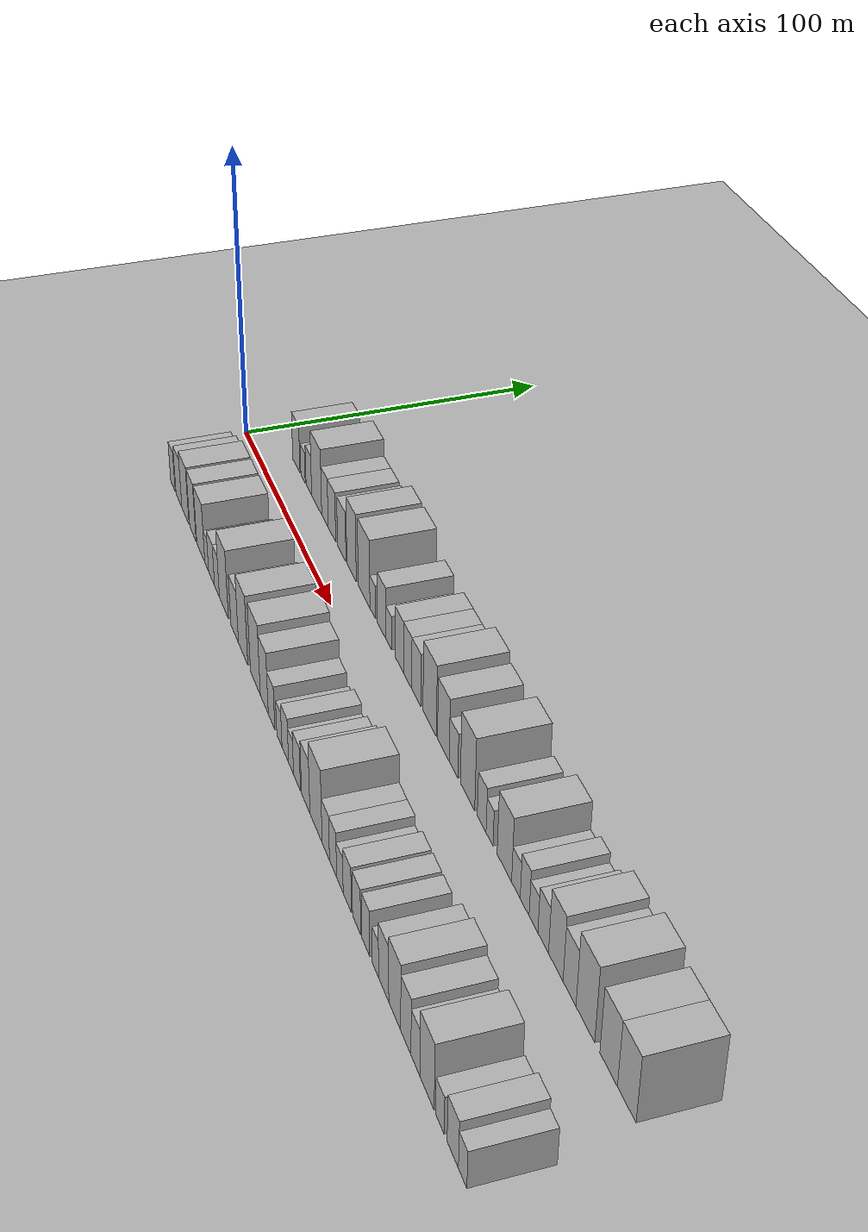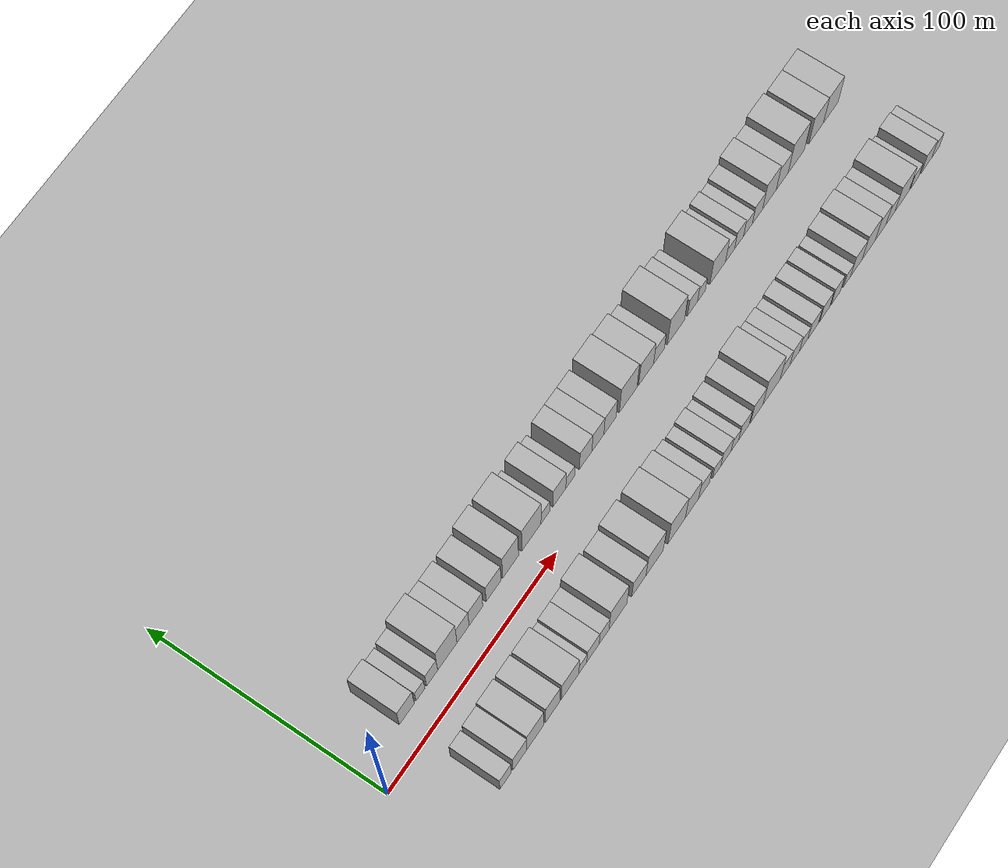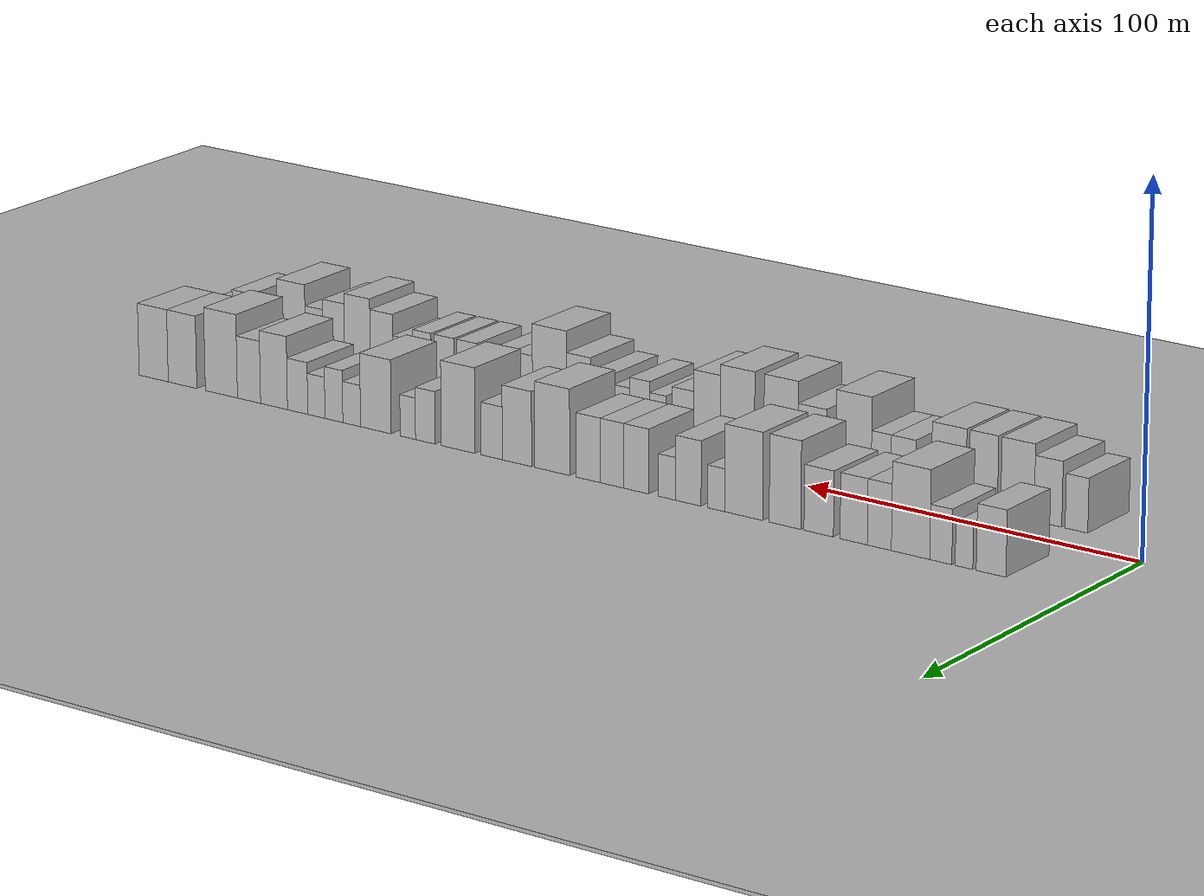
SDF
<?xml version="1.0" encoding="utf-8"?>

<sdf version="1.6">

   <world name="default">

      <gui fullscreen="0">

         <camera name="user_camera">

            <pose>-15 0 4.57585 0 0 0</pose>

            <view_controller>orbit</view_controller>

         </camera>

      </gui>

      <scene>

         <sky>

           <clouds>

             <speed>12</speed>

           </clouds>

         </sky>

         <ambient>0.4 0.4 0.4 1</ambient>

         <background>0.7 0.7 0.7 1</background>

         <shadows>1</shadows>

      </scene>

      <gravity>0 0 -9.8066</gravity>

      <magnetic_field>6e-06 2.3e-05 -4.2e-05</magnetic_field>

      <physics default="0" name="default_physics" type="ode">

         <ode>

            <solver>

               <type>quick</type>

               <iters>10</iters>

               <sor>1.0</sor>

               <use_dynamic_moi_rescaling>0</use_dynamic_moi_rescaling>

            </solver>

            <constraints>

               <cfm>0</cfm>

               <erp>0.2</erp>

               <contact_max_correcting_vel>100</contact_max_correcting_vel>

               <contact_surface_layer>0.001</contact_surface_layer>

            </constraints>

         </ode>

         <max_step_size>0.004</max_step_size>

         <real_time_factor>1</real_time_factor>

         <real_time_update_rate>250</real_time_update_rate>

      </physics>

      <light name="sun" type="directional">

         <cast_shadows>1</cast_shadows>

         <pose>0 0 10 0 0 0</pose>

         <diffuse>0.8 0.8 0.8 1</diffuse>

         <specular>0.2 0.2 0.2 1</specular>

         <attenuation>

            <range>1000</range>

            <constant>0.9</constant>

            <linear>0.01</linear>

            <quadratic>0.001</quadratic>

         </attenuation>

         <direction>-0.5 0.1 -0.9</direction>

      </light>

      <include>

         <name>ground_plane_1</name>

         <uri>model://HANNAS_ground_plane</uri>

         <pose>0 0 0  0 0 0</pose>

      </include>

      <include>

         <name>ground_plane_2</name>

         <uri>model://HANNAS_ground_plane</uri>

         <pose>100 0 0  0 0 0</pose>

      </include>

      <model name="building_1">

         <static>1</static>

         <pose frame="">25.3415 20.0000 0 0.000000 0.000000 1.570796</pose>

         <link name="link">

            <pose frame="">0 0 9.00 0 0 0</pose>

            <collision name="collision">

               <geometry>

                  <box>

                     <size>20.0000 8.6830 18.0000</size>

                  </box>

               </geometry>

               <max_contacts>10</max_contacts>

               <surface>

                  <contact>

                     <ode/>

                  </contact>

                  <bounce/>

                  <friction>

                     <torsional>

                        <ode/>

                     </torsional>

                     <ode/>

                  </friction>

               </surface>

            </collision>

            <visual name="visual">

               <cast_shadows>0</cast_shadows>

               <geometry>

                  <box>

                     <size>20.0000 8.6830 18.0000</size>

                  </box>

               </geometry>

               <material>

                  <script>

                     <uri>model://HANNAS_wall/materials/scripts</uri>

                     <uri>model://HANNAS_wall/materials/textures</uri>

                     <name>vrc/HANNAS_wall</name>

                  </script>

               </material>

            </visual>

            <self_collide>0</self_collide>

            <enable_wind>0</enable_wind>

            <kinematic>0</kinematic>

         </link>

      </model>

      <model name="building_2">

         <static>1</static>

         <pose frame="">33.2663 20.0000 0 0.000000 0.000000 1.570796</pose>

         <link name="link">

            <pose frame="">0 0 6.00 0 0 0</pose>

            <collision name="collision">

               <geometry>

                  <box>

                     <size>20.0000 5.1667 12.0000</size>

                  </box>

               </geometry>

               <max_contacts>10</max_contacts>

               <surface>

                  <contact>

                     <ode/>

                  </contact>

                  <bounce/>

                  <friction>

                     <torsional>

                        <ode/>

                     </torsional>

                     <ode/>

                  </friction>

               </surface>

            </collision>

            <visual name="visual">

               <cast_shadows>0</cast_shadows>

               <geometry>

                  <box>

                     <size>20.0000 5.1667 12.0000</size>

                  </box>

               </geometry>

               <material>

                  <script>

                     <uri>model://HANNAS_wall/materials/scripts</uri>

                     <uri>model://HANNAS_wall/materials/textures</uri>

                     <name>vrc/HANNAS_wall</name>

                  </script>

               </material>

            </visual>

            <self_collide>0</self_collide>

            <enable_wind>0</enable_wind>

            <kinematic>0</kinematic>

         </link>

      </model>

      <model name="building_3">

         <static>1</static>

         <pose frame="">40.0961 20.0000 0 0.000000 0.000000 1.570796</pose>

         <link name="link">

            <pose frame="">0 0 7.50 0 0 0</pose>

            <collision name="collision">

               <geometry>

                  <box>

                     <size>20.0000 6.4929 15.0000</size>

                  </box>

               </geometry>

               <max_contacts>10</max_contacts>

               <surface>

                  <contact>

                     <ode/>

                  </contact>

                  <bounce/>

                  <friction>

                     <torsional>

                        <ode/>

                     </torsional>

                     <ode/>

                  </friction>

               </surface>

            </collision>

            <visual name="visual">

               <cast_shadows>0</cast_shadows>

               <geometry>

                  <box>

                     <size>20.0000 6.4929 15.0000</size>

                  </box>

               </geometry>

               <material>

                  <script>

                     <uri>model://HANNAS_wall/materials/scripts</uri>

                     <uri>model://HANNAS_wall/materials/textures</uri>

                     <name>vrc/HANNAS_wall</name>

                  </script>

               </material>

            </visual>

            <self_collide>0</self_collide>

            <enable_wind>0</enable_wind>

            <kinematic>0</kinematic>

         </link>

      </model>

      <model name="building_4">

         <static>1</static>

         <pose frame="">49.0467 20.0000 0 0.000000 0.000000 1.570796</pose>

         <link name="link">

            <pose frame="">0 0 12.00 0 0 0</pose>

            <collision name="collision">

               <geometry>

                  <box>

                     <size>20.0000 11.4082 24.0000</size>

                  </box>

               </geometry>

               <max_contacts>10</max_contacts>

               <surface>

                  <contact>

                     <ode/>

                  </contact>

                  <bounce/>

                  <friction>

                     <torsional>

                        <ode/>

                     </torsional>

                     <ode/>

                  </friction>

               </surface>

            </collision>

            <visual name="visual">

               <cast_shadows>0</cast_shadows>

               <geometry>

                  <box>

                     <size>20.0000 11.4082 24.0000</size>

                  </box>

               </geometry>

               <material>

                  <script>

                     <uri>model://HANNAS_wall/materials/scripts</uri>

                     <uri>model://HANNAS_wall/materials/textures</uri>

                     <name>vrc/HANNAS_wall</name>

                  </script>

               </material>

            </visual>

            <self_collide>0</self_collide>

            <enable_wind>0</enable_wind>

            <kinematic>0</kinematic>

         </link>

      </model>

      <model name="building_5">

         <static>1</static>

         <pose frame="">58.3521 20.0000 0 0.000000 0.000000 1.570796</pose>

         <link name="link">

            <pose frame="">0 0 9.00 0 0 0</pose>

            <collision name="collision">

               <geometry>

                  <box>

                     <size>20.0000 7.2025 18.0000</size>

                  </box>

               </geometry>

               <max_contacts>10</max_contacts>

               <surface>

                  <contact>

                     <ode/>

                  </contact>

                  <bounce/>

                  <friction>

                     <torsional>

                        <ode/>

                     </torsional>

                     <ode/>

                  </friction>

               </surface>

            </collision>

            <visual name="visual">

               <cast_shadows>0</cast_shadows>

               <geometry>

                  <box>

                     <size>20.0000 7.2025 18.0000</size>

                  </box>

               </geometry>

               <material>

                  <script>

                     <uri>model://HANNAS_wall/materials/scripts</uri>

                     <uri>model://HANNAS_wall/materials/textures</uri>

                     <name>vrc/HANNAS_wall</name>

                  </script>

               </material>

            </visual>

            <self_collide>0</self_collide>

            <enable_wind>0</enable_wind>

            <kinematic>0</kinematic>

         </link>

      </model>

      <model name="building_6">

         <static>1</static>

         <pose frame="">66.0468 20.0000 0 0.000000 0.000000 1.570796</pose>

         <link name="link">

            <pose frame="">0 0 9.00 0 0 0</pose>

            <collision name="collision">

               <geometry>

                  <box>

                     <size>20.0000 8.1869 18.0000</size>

                  </box>

               </geometry>

               <max_contacts>10</max_contacts>

               <surface>

                  <contact>

                     <ode/>

                  </contact>

                  <bounce/>

                  <friction>

                     <torsional>

                        <ode/>

                     </torsional>

                     <ode/>

                  </friction>

               </surface>

            </collision>

            <visual name="visual">

               <cast_shadows>0</cast_shadows>

               <geometry>

                  <box>

                     <size>20.0000 8.1869 18.0000</size>

                  </box>

               </geometry>

               <material>

                  <script>

                     <uri>model://HANNAS_wall/materials/scripts</uri>

                     <uri>model://HANNAS_wall/materials/textures</uri>

                     <name>vrc/HANNAS_wall</name>

                  </script>

               </material>

            </visual>

            <self_collide>0</self_collide>

            <enable_wind>0</enable_wind>

            <kinematic>0</kinematic>

         </link>

      </model>

      <model name="building_7">

         <static>1</static>

         <pose frame="">76.6029 20.0000 0 0.000000 0.000000 1.570796</pose>

         <link name="link">

            <pose frame="">0 0 9.00 0 0 0</pose>

            <collision name="collision">

               <geometry>

                  <box>

                     <size>20.0000 8.9252 18.0000</size>

                  </box>

               </geometry>

               <max_contacts>10</max_contacts>

               <surface>

                  <contact>

                     <ode/>

                  </contact>

                  <bounce/>

                  <friction>

                     <torsional>

                        <ode/>

                     </torsional>

                     <ode/>

                  </friction>

               </surface>

            </collision>

            <visual name="visual">

               <cast_shadows>0</cast_shadows>

               <geometry>

                  <box>

                     <size>20.0000 8.9252 18.0000</size>

                  </box>

               </geometry>

               <material>

                  <script>

                     <uri>model://HANNAS_wall/materials/scripts</uri>

                     <uri>model://HANNAS_wall/materials/textures</uri>

                     <name>vrc/HANNAS_wall</name>

                  </script>

               </material>

            </visual>

            <self_collide>0</self_collide>

            <enable_wind>0</enable_wind>

            <kinematic>0</kinematic>

         </link>

      </model>

      <model name="building_8">

         <static>1</static>

         <pose frame="">86.8832 20.0000 0 0.000000 0.000000 1.570796</pose>

         <link name="link">

            <pose frame="">0 0 12.00 0 0 0</pose>

            <collision name="collision">

               <geometry>

                  <box>

                     <size>20.0000 9.6355 24.0000</size>

                  </box>

               </geometry>

               <max_contacts>10</max_contacts>

               <surface>

                  <contact>

                     <ode/>

                  </contact>

                  <bounce/>

                  <friction>

                     <torsional>

                        <ode/>

                     </torsional>

                     <ode/>

                  </friction>

               </surface>

            </collision>

            <visual name="visual">

               <cast_shadows>0</cast_shadows>

               <geometry>

                  <box>

                     <size>20.0000 9.6355 24.0000</size>

                  </box>

               </geometry>

               <material>

                  <script>

                     <uri>model://HANNAS_wall/materials/scripts</uri>

                     <uri>model://HANNAS_wall/materials/textures</uri>

                     <name>vrc/HANNAS_wall</name>

                  </script>

               </material>

            </visual>

            <self_collide>0</self_collide>

            <enable_wind>0</enable_wind>

            <kinematic>0</kinematic>

         </link>

      </model>

      <model name="building_9">

         <static>1</static>

         <pose frame="">99.5599 20.0000 0 0.000000 0.000000 1.570796</pose>

         <link name="link">

            <pose frame="">0 0 12.00 0 0 0</pose>

            <collision name="collision">

               <geometry>

                  <box>

                     <size>20.0000 11.7179 24.0000</size>

                  </box>

               </geometry>

               <max_contacts>10</max_contacts>

               <surface>

                  <contact>

                     <ode/>

                  </contact>

                  <bounce/>

                  <friction>

                     <torsional>

                        <ode/>

                     </torsional>

                     <ode/>

                  </friction>

               </surface>

            </collision>

            <visual name="visual">

               <cast_shadows>0</cast_shadows>

               <geometry>

                  <box>

                     <size>20.0000 11.7179 24.0000</size>

                  </box>

               </geometry>

               <material>

                  <script>

                     <uri>model://HANNAS_wall/materials/scripts</uri>

                     <uri>model://HANNAS_wall/materials/textures</uri>

                     <name>vrc/HANNAS_wall</name>

                  </script>

               </material>

            </visual>

            <self_collide>0</self_collide>

            <enable_wind>0</enable_wind>

            <kinematic>0</kinematic>

         </link>

      </model>

      <model name="building_10">

         <static>1</static>

         <pose frame="">108.0974 20.0000 0 0.000000 0.000000 1.570796</pose>

         <link name="link">

            <pose frame="">0 0 6.00 0 0 0</pose>

            <collision name="collision">

               <geometry>

                  <box>

                     <size>20.0000 5.3571 12.0000</size>

                  </box>

               </geometry>

               <max_contacts>10</max_contacts>

               <surface>

                  <contact>

                     <ode/>

                  </contact>

                  <bounce/>

                  <friction>

                     <torsional>

                        <ode/>

                     </torsional>

                     <ode/>

                  </friction>

               </surface>

            </collision>

            <visual name="visual">

               <cast_shadows>0</cast_shadows>

               <geometry>

                  <box>

                     <size>20.0000 5.3571 12.0000</size>

                  </box>

               </geometry>

               <material>

                  <script>

                     <uri>model://HANNAS_wall/materials/scripts</uri>

                     <uri>model://HANNAS_wall/materials/textures</uri>

                     <name>vrc/HANNAS_wall</name>

                  </script>

               </material>

            </visual>

            <self_collide>0</self_collide>

            <enable_wind>0</enable_wind>

            <kinematic>0</kinematic>

         </link>

      </model>

      <model name="building_11">

         <static>1</static>

         <pose frame="">116.7581 20.0000 0 0.000000 0.000000 1.570796</pose>

         <link name="link">

            <pose frame="">0 0 9.00 0 0 0</pose>

            <collision name="collision">

               <geometry>

                  <box>

                     <size>20.0000 7.9643 18.0000</size>

                  </box>

               </geometry>

               <max_contacts>10</max_contacts>

               <surface>

                  <contact>

                     <ode/>

                  </contact>

                  <bounce/>

                  <friction>

                     <torsional>

                        <ode/>

                     </torsional>

                     <ode/>

                  </friction>

               </surface>

            </collision>

            <visual name="visual">

               <cast_shadows>0</cast_shadows>

               <geometry>

                  <box>

                     <size>20.0000 7.9643 18.0000</size>

                  </box>

               </geometry>

               <material>

                  <script>

                     <uri>model://HANNAS_wall/materials/scripts</uri>

                     <uri>model://HANNAS_wall/materials/textures</uri>

                     <name>vrc/HANNAS_wall</name>

                  </script>

               </material>

            </visual>

            <self_collide>0</self_collide>

            <enable_wind>0</enable_wind>

            <kinematic>0</kinematic>

         </link>

      </model>

      <model name="building_12">

         <static>1</static>

         <pose frame="">123.4481 20.0000 0 0.000000 0.000000 1.570796</pose>

         <link name="link">

            <pose frame="">0 0 6.00 0 0 0</pose>

            <collision name="collision">

               <geometry>

                  <box>

                     <size>20.0000 5.4156 12.0000</size>

                  </box>

               </geometry>

               <max_contacts>10</max_contacts>

               <surface>

                  <contact>

                     <ode/>

                  </contact>

                  <bounce/>

                  <friction>

                     <torsional>

                        <ode/>

                     </torsional>

                     <ode/>

                  </friction>

               </surface>

            </collision>

            <visual name="visual">

               <cast_shadows>0</cast_shadows>

               <geometry>

                  <box>

                     <size>20.0000 5.4156 12.0000</size>

                  </box>

               </geometry>

               <material>

                  <script>

                     <uri>model://HANNAS_wall/materials/scripts</uri>

                     <uri>model://HANNAS_wall/materials/textures</uri>

                     <name>vrc/HANNAS_wall</name>

                  </script>

               </material>

            </visual>

            <self_collide>0</self_collide>

            <enable_wind>0</enable_wind>

            <kinematic>0</kinematic>

         </link>

      </model>

      <model name="building_13">

         <static>1</static>

         <pose frame="">133.0971 20.0000 0 0.000000 0.000000 1.570796</pose>

         <link name="link">

            <pose frame="">0 0 9.00 0 0 0</pose>

            <collision name="collision">

               <geometry>

                  <box>

                     <size>20.0000 7.8824 18.0000</size>

                  </box>

               </geometry>

               <max_contacts>10</max_contacts>

               <surface>

                  <contact>

                     <ode/>

                  </contact>

                  <bounce/>

                  <friction>

                     <torsional>

                        <ode/>

                     </torsional>

                     <ode/>

                  </friction>

               </surface>

            </collision>

            <visual name="visual">

               <cast_shadows>0</cast_shadows>

               <geometry>

                  <box>

                     <size>20.0000 7.8824 18.0000</size>

                  </box>

               </geometry>

               <material>

                  <script>

                     <uri>model://HANNAS_wall/materials/scripts</uri>

                     <uri>model://HANNAS_wall/materials/textures</uri>

                     <name>vrc/HANNAS_wall</name>

                  </script>

               </material>

            </visual>

            <self_collide>0</self_collide>

            <enable_wind>0</enable_wind>

            <kinematic>0</kinematic>

         </link>

      </model>

      <model name="building_14">

         <static>1</static>

         <pose frame="">140.7714 20.0000 0 0.000000 0.000000 1.570796</pose>

         <link name="link">

            <pose frame="">0 0 9.00 0 0 0</pose>

            <collision name="collision">

               <geometry>

                  <box>

                     <size>20.0000 7.4662 18.0000</size>

                  </box>

               </geometry>

               <max_contacts>10</max_contacts>

               <surface>

                  <contact>

                     <ode/>

                  </contact>

                  <bounce/>

                  <friction>

                     <torsional>

                        <ode/>

                     </torsional>

                     <ode/>

                  </friction>

               </surface>

            </collision>

            <visual name="visual">

               <cast_shadows>0</cast_shadows>

               <geometry>

                  <box>

                     <size>20.0000 7.4662 18.0000</size>

                  </box>

               </geometry>

               <material>

                  <script>

                     <uri>model://HANNAS_wall/materials/scripts</uri>

                     <uri>model://HANNAS_wall/materials/textures</uri>

                     <name>vrc/HANNAS_wall</name>

                  </script>

               </material>

            </visual>

            <self_collide>0</self_collide>

            <enable_wind>0</enable_wind>

            <kinematic>0</kinematic>

         </link>

      </model>

      <model name="building_15">

         <static>1</static>

         <pose frame="">148.4154 20.0000 0 0.000000 0.000000 1.570796</pose>

         <link name="link">

            <pose frame="">0 0 9.00 0 0 0</pose>

            <collision name="collision">

               <geometry>

                  <box>

                     <size>20.0000 7.8217 18.0000</size>

                  </box>

               </geometry>

               <max_contacts>10</max_contacts>

               <surface>

                  <contact>

                     <ode/>

                  </contact>

                  <bounce/>

                  <friction>

                     <torsional>

                        <ode/>

                     </torsional>

                     <ode/>

                  </friction>

               </surface>

            </collision>

            <visual name="visual">

               <cast_shadows>0</cast_shadows>

               <geometry>

                  <box>

                     <size>20.0000 7.8217 18.0000</size>

                  </box>

               </geometry>

               <material>

                  <script>

                     <uri>model://HANNAS_wall/materials/scripts</uri>

                     <uri>model://HANNAS_wall/materials/textures</uri>

                     <name>vrc/HANNAS_wall</name>

                  </script>

               </material>

            </visual>

            <self_collide>0</self_collide>

            <enable_wind>0</enable_wind>

            <kinematic>0</kinematic>

         </link>

      </model>

      <model name="building_16">

         <static>1</static>

         <pose frame="">159.9674 20.0000 0 0.000000 0.000000 1.570796</pose>

         <link name="link">

            <pose frame="">0 0 12.00 0 0 0</pose>

            <collision name="collision">

               <geometry>

                  <box>

                     <size>20.0000 11.2824 24.0000</size>

                  </box>

               </geometry>

               <max_contacts>10</max_contacts>

               <surface>

                  <contact>

                     <ode/>

                  </contact>

                  <bounce/>

                  <friction>

                     <torsional>

                        <ode/>

                     </torsional>

                     <ode/>

                  </friction>

               </surface>

            </collision>

            <visual name="visual">

               <cast_shadows>0</cast_shadows>

               <geometry>

                  <box>

                     <size>20.0000 11.2824 24.0000</size>

                  </box>

               </geometry>

               <material>

                  <script>

                     <uri>model://HANNAS_wall/materials/scripts</uri>

                     <uri>model://HANNAS_wall/materials/textures</uri>

                     <name>vrc/HANNAS_wall</name>

                  </script>

               </material>

            </visual>

            <self_collide>0</self_collide>

            <enable_wind>0</enable_wind>

            <kinematic>0</kinematic>

         </link>

      </model>

      <model name="building_17">

         <static>1</static>

         <pose frame="">171.3754 20.0000 0 0.000000 0.000000 1.570796</pose>

         <link name="link">

            <pose frame="">0 0 10.50 0 0 0</pose>

            <collision name="collision">

               <geometry>

                  <box>

                     <size>20.0000 9.5335 21.0000</size>

                  </box>

               </geometry>

               <max_contacts>10</max_contacts>

               <surface>

                  <contact>

                     <ode/>

                  </contact>

                  <bounce/>

                  <friction>

                     <torsional>

                        <ode/>

                     </torsional>

                     <ode/>

                  </friction>

               </surface>

            </collision>

            <visual name="visual">

               <cast_shadows>0</cast_shadows>

               <geometry>

                  <box>

                     <size>20.0000 9.5335 21.0000</size>

                  </box>

               </geometry>

               <material>

                  <script>

                     <uri>model://HANNAS_wall/materials/scripts</uri>

                     <uri>model://HANNAS_wall/materials/textures</uri>

                     <name>vrc/HANNAS_wall</name>

                  </script>

               </material>

            </visual>

            <self_collide>0</self_collide>

            <enable_wind>0</enable_wind>

            <kinematic>0</kinematic>

         </link>

      </model>

      <model name="building_18">

         <static>1</static>

         <pose frame="">179.6254 20.0000 0 0.000000 0.000000 1.570796</pose>

         <link name="link">

            <pose frame="">0 0 7.50 0 0 0</pose>

            <collision name="collision">

               <geometry>

                  <box>

                     <size>20.0000 6.9665 15.0000</size>

                  </box>

               </geometry>

               <max_contacts>10</max_contacts>

               <surface>

                  <contact>

                     <ode/>

                  </contact>

                  <bounce/>

                  <friction>

                     <torsional>

                        <ode/>

                     </torsional>

                     <ode/>

                  </friction>

               </surface>

            </collision>

            <visual name="visual">

               <cast_shadows>0</cast_shadows>

               <geometry>

                  <box>

                     <size>20.0000 6.9665 15.0000</size>

                  </box>

               </geometry>

               <material>

                  <script>

                     <uri>model://HANNAS_wall/materials/scripts</uri>

                     <uri>model://HANNAS_wall/materials/textures</uri>

                     <name>vrc/HANNAS_wall</name>

                  </script>

               </material>

            </visual>

            <self_collide>0</self_collide>

            <enable_wind>0</enable_wind>

            <kinematic>0</kinematic>

         </link>

      </model>

      <model name="building_19">

         <static>1</static>

         <pose frame="">190.6612 20.0000 0 0.000000 0.000000 1.570796</pose>

         <link name="link">

            <pose frame="">0 0 12.00 0 0 0</pose>

            <collision name="collision">

               <geometry>

                  <box>

                     <size>20.0000 11.1052 24.0000</size>

                  </box>

               </geometry>

               <max_contacts>10</max_contacts>

               <surface>

                  <contact>

                     <ode/>

                  </contact>

                  <bounce/>

                  <friction>

                     <torsional>

                        <ode/>

                     </torsional>

                     <ode/>

                  </friction>

               </surface>

            </collision>

            <visual name="visual">

               <cast_shadows>0</cast_shadows>

               <geometry>

                  <box>

                     <size>20.0000 11.1052 24.0000</size>

                  </box>

               </geometry>

               <material>

                  <script>

                     <uri>model://HANNAS_wall/materials/scripts</uri>

                     <uri>model://HANNAS_wall/materials/textures</uri>

                     <name>vrc/HANNAS_wall</name>

                  </script>

               </material>

            </visual>

            <self_collide>0</self_collide>

            <enable_wind>0</enable_wind>

            <kinematic>0</kinematic>

         </link>

      </model>

      <model name="building_20">

         <static>1</static>

         <pose frame="">201.5022 20.0000 0 0.000000 0.000000 1.570796</pose>

         <link name="link">

            <pose frame="">0 0 7.50 0 0 0</pose>

            <collision name="collision">

               <geometry>

                  <box>

                     <size>20.0000 6.5768 15.0000</size>

                  </box>

               </geometry>

               <max_contacts>10</max_contacts>

               <surface>

                  <contact>

                     <ode/>

                  </contact>

                  <bounce/>

                  <friction>

                     <torsional>

                        <ode/>

                     </torsional>

                     <ode/>

                  </friction>

               </surface>

            </collision>

            <visual name="visual">

               <cast_shadows>0</cast_shadows>

               <geometry>

                  <box>

                     <size>20.0000 6.5768 15.0000</size>

                  </box>

               </geometry>

               <material>

                  <script>

                     <uri>model://HANNAS_wall/materials/scripts</uri>

                     <uri>model://HANNAS_wall/materials/textures</uri>

                     <name>vrc/HANNAS_wall</name>

                  </script>

               </material>

            </visual>

            <self_collide>0</self_collide>

            <enable_wind>0</enable_wind>

            <kinematic>0</kinematic>

         </link>

      </model>

      <model name="building_21">

         <static>1</static>

         <pose frame="">207.3468 20.0000 0 0.000000 0.000000 1.570796</pose>

         <link name="link">

            <pose frame="">0 0 6.00 0 0 0</pose>

            <collision name="collision">

               <geometry>

                  <box>

                     <size>20.0000 5.1124 12.0000</size>

                  </box>

               </geometry>

               <max_contacts>10</max_contacts>

               <surface>

                  <contact>

                     <ode/>

                  </contact>

                  <bounce/>

                  <friction>

                     <torsional>

                        <ode/>

                     </torsional>

                     <ode/>

                  </friction>

               </surface>

            </collision>

            <visual name="visual">

               <cast_shadows>0</cast_shadows>

               <geometry>

                  <box>

                     <size>20.0000 5.1124 12.0000</size>

                  </box>

               </geometry>

               <material>

                  <script>

                     <uri>model://HANNAS_wall/materials/scripts</uri>

                     <uri>model://HANNAS_wall/materials/textures</uri>

                     <name>vrc/HANNAS_wall</name>

                  </script>

               </material>

            </visual>

            <self_collide>0</self_collide>

            <enable_wind>0</enable_wind>

            <kinematic>0</kinematic>

         </link>

      </model>

      <model name="building_22">

         <static>1</static>

         <pose frame="">218.0613 20.0000 0 0.000000 0.000000 1.570796</pose>

         <link name="link">

            <pose frame="">0 0 10.50 0 0 0</pose>

            <collision name="collision">

               <geometry>

                  <box>

                     <size>20.0000 10.3166 21.0000</size>

                  </box>

               </geometry>

               <max_contacts>10</max_contacts>

               <surface>

                  <contact>

                     <ode/>

                  </contact>

                  <bounce/>

                  <friction>

                     <torsional>

                        <ode/>

                     </torsional>

                     <ode/>

                  </friction>

               </surface>

            </collision>

            <visual name="visual">

               <cast_shadows>0</cast_shadows>

               <geometry>

                  <box>

                     <size>20.0000 10.3166 21.0000</size>

                  </box>

               </geometry>

               <material>

                  <script>

                     <uri>model://HANNAS_wall/materials/scripts</uri>

                     <uri>model://HANNAS_wall/materials/textures</uri>

                     <name>vrc/HANNAS_wall</name>

                  </script>

               </material>

            </visual>

            <self_collide>0</self_collide>

            <enable_wind>0</enable_wind>

            <kinematic>0</kinematic>

         </link>

      </model>

      <model name="building_23">

         <static>1</static>

         <pose frame="">226.2164 20.0000 0 0.000000 0.000000 1.570796</pose>

         <link name="link">

            <pose frame="">0 0 6.00 0 0 0</pose>

            <collision name="collision">

               <geometry>

                  <box>

                     <size>20.0000 5.9935 12.0000</size>

                  </box>

               </geometry>

               <max_contacts>10</max_contacts>

               <surface>

                  <contact>

                     <ode/>

                  </contact>

                  <bounce/>

                  <friction>

                     <torsional>

                        <ode/>

                     </torsional>

                     <ode/>

                  </friction>

               </surface>

            </collision>

            <visual name="visual">

               <cast_shadows>0</cast_shadows>

               <geometry>

                  <box>

                     <size>20.0000 5.9935 12.0000</size>

                  </box>

               </geometry>

               <material>

                  <script>

                     <uri>model://HANNAS_wall/materials/scripts</uri>

                     <uri>model://HANNAS_wall/materials/textures</uri>

                     <name>vrc/HANNAS_wall</name>

                  </script>

               </material>

            </visual>

            <self_collide>0</self_collide>

            <enable_wind>0</enable_wind>

            <kinematic>0</kinematic>

         </link>

      </model>

      <model name="building_24">

         <static>1</static>

         <pose frame="">232.2508 20.0000 0 0.000000 0.000000 1.570796</pose>

         <link name="link">

            <pose frame="">0 0 7.50 0 0 0</pose>

            <collision name="collision">

               <geometry>

                  <box>

                     <size>20.0000 6.0754 15.0000</size>

                  </box>

               </geometry>

               <max_contacts>10</max_contacts>

               <surface>

                  <contact>

                     <ode/>

                  </contact>

                  <bounce/>

                  <friction>

                     <torsional>

                        <ode/>

                     </torsional>

                     <ode/>

                  </friction>

               </surface>

            </collision>

            <visual name="visual">

               <cast_shadows>0</cast_shadows>

               <geometry>

                  <box>

                     <size>20.0000 6.0754 15.0000</size>

                  </box>

               </geometry>

               <material>

                  <script>

                     <uri>model://HANNAS_wall/materials/scripts</uri>

                     <uri>model://HANNAS_wall/materials/textures</uri>

                     <name>vrc/HANNAS_wall</name>

                  </script>

               </material>

            </visual>

            <self_collide>0</self_collide>

            <enable_wind>0</enable_wind>

            <kinematic>0</kinematic>

         </link>

      </model>

      <model name="building_25">

         <static>1</static>

         <pose frame="">238.2232 20.0000 0 0.000000 0.000000 1.570796</pose>

         <link name="link">

            <pose frame="">0 0 6.00 0 0 0</pose>

            <collision name="collision">

               <geometry>

                  <box>

                     <size>20.0000 5.8694 12.0000</size>

                  </box>

               </geometry>

               <max_contacts>10</max_contacts>

               <surface>

                  <contact>

                     <ode/>

                  </contact>

                  <bounce/>

                  <friction>

                     <torsional>

                        <ode/>

                     </torsional>

                     <ode/>

                  </friction>

               </surface>

            </collision>

            <visual name="visual">

               <cast_shadows>0</cast_shadows>

               <geometry>

                  <box>

                     <size>20.0000 5.8694 12.0000</size>

                  </box>

               </geometry>

               <material>

                  <script>

                     <uri>model://HANNAS_wall/materials/scripts</uri>

                     <uri>model://HANNAS_wall/materials/textures</uri>

                     <name>vrc/HANNAS_wall</name>

                  </script>

               </material>

            </visual>

            <self_collide>0</self_collide>

            <enable_wind>0</enable_wind>

            <kinematic>0</kinematic>

         </link>

      </model>

      <model name="building_26">

         <static>1</static>

         <pose frame="">244.6414 20.0000 0 0.000000 0.000000 1.570796</pose>

         <link name="link">

            <pose frame="">0 0 7.50 0 0 0</pose>

            <collision name="collision">

               <geometry>

                  <box>

                     <size>20.0000 6.9671 15.0000</size>

                  </box>

               </geometry>

               <max_contacts>10</max_contacts>

               <surface>

                  <contact>

                     <ode/>

                  </contact>

                  <bounce/>

                  <friction>

                     <torsional>

                        <ode/>

                     </torsional>

                     <ode/>

                  </friction>

               </surface>

            </collision>

            <visual name="visual">

               <cast_shadows>0</cast_shadows>

               <geometry>

                  <box>

                     <size>20.0000 6.9671 15.0000</size>

                  </box>

               </geometry>

               <material>

                  <script>

                     <uri>model://HANNAS_wall/materials/scripts</uri>

                     <uri>model://HANNAS_wall/materials/textures</uri>

                     <name>vrc/HANNAS_wall</name>

                  </script>

               </material>

            </visual>

            <self_collide>0</self_collide>

            <enable_wind>0</enable_wind>

            <kinematic>0</kinematic>

         </link>

      </model>

      <model name="building_27">

         <static>1</static>

         <pose frame="">252.7623 20.0000 0 0.000000 0.000000 1.570796</pose>

         <link name="link">

            <pose frame="">0 0 10.50 0 0 0</pose>

            <collision name="collision">

               <geometry>

                  <box>

                     <size>20.0000 9.2746 21.0000</size>

                  </box>

               </geometry>

               <max_contacts>10</max_contacts>

               <surface>

                  <contact>

                     <ode/>

                  </contact>

                  <bounce/>

                  <friction>

                     <torsional>

                        <ode/>

                     </torsional>

                     <ode/>

                  </friction>

               </surface>

            </collision>

            <visual name="visual">

               <cast_shadows>0</cast_shadows>

               <geometry>

                  <box>

                     <size>20.0000 9.2746 21.0000</size>

                  </box>

               </geometry>

               <material>

                  <script>

                     <uri>model://HANNAS_wall/materials/scripts</uri>

                     <uri>model://HANNAS_wall/materials/textures</uri>

                     <name>vrc/HANNAS_wall</name>

                  </script>

               </material>

            </visual>

            <self_collide>0</self_collide>

            <enable_wind>0</enable_wind>

            <kinematic>0</kinematic>

         </link>

      </model>

      <model name="building_28">

         <static>1</static>

         <pose frame="">261.4188 20.0000 0 0.000000 0.000000 1.570796</pose>

         <link name="link">

            <pose frame="">0 0 9.00 0 0 0</pose>

            <collision name="collision">

               <geometry>

                  <box>

                     <size>20.0000 8.0386 18.0000</size>

                  </box>

               </geometry>

               <max_contacts>10</max_contacts>

               <surface>

                  <contact>

                     <ode/>

                  </contact>

                  <bounce/>

                  <friction>

                     <torsional>

                        <ode/>

                     </torsional>

                     <ode/>

                  </friction>

               </surface>

            </collision>

            <visual name="visual">

               <cast_shadows>0</cast_shadows>

               <geometry>

                  <box>

                     <size>20.0000 8.0386 18.0000</size>

                  </box>

               </geometry>

               <material>

                  <script>

                     <uri>model://HANNAS_wall/materials/scripts</uri>

                     <uri>model://HANNAS_wall/materials/textures</uri>

                     <name>vrc/HANNAS_wall</name>

                  </script>

               </material>

            </visual>

            <self_collide>0</self_collide>

            <enable_wind>0</enable_wind>

            <kinematic>0</kinematic>

         </link>

      </model>

      <model name="building_29">

         <static>1</static>

         <pose frame="">271.0423 20.0000 0 0.000000 0.000000 1.570796</pose>

         <link name="link">

            <pose frame="">0 0 12.00 0 0 0</pose>

            <collision name="collision">

               <geometry>

                  <box>

                     <size>20.0000 11.2085 24.0000</size>

                  </box>

               </geometry>

               <max_contacts>10</max_contacts>

               <surface>

                  <contact>

                     <ode/>

                  </contact>

                  <bounce/>

                  <friction>

                     <torsional>

                        <ode/>

                     </torsional>

                     <ode/>

                  </friction>

               </surface>

            </collision>

            <visual name="visual">

               <cast_shadows>0</cast_shadows>

               <geometry>

                  <box>

                     <size>20.0000 11.2085 24.0000</size>

                  </box>

               </geometry>

               <material>

                  <script>

                     <uri>model://HANNAS_wall/materials/scripts</uri>

                     <uri>model://HANNAS_wall/materials/textures</uri>

                     <name>vrc/HANNAS_wall</name>

                  </script>

               </material>

            </visual>

            <self_collide>0</self_collide>

            <enable_wind>0</enable_wind>

            <kinematic>0</kinematic>

         </link>

      </model>

      <model name="building_30">

         <static>1</static>

         <pose frame="">284.6836 20.0000 0 0.000000 0.000000 1.570796</pose>

         <link name="link">

            <pose frame="">0 0 10.50 0 0 0</pose>

            <collision name="collision">

               <geometry>

                  <box>

                     <size>20.0000 10.0740 21.0000</size>

                  </box>

               </geometry>

               <max_contacts>10</max_contacts>

               <surface>

                  <contact>

                     <ode/>

                  </contact>

                  <bounce/>

                  <friction>

                     <torsional>

                        <ode/>

                     </torsional>

                     <ode/>

                  </friction>

               </surface>

            </collision>

            <visual name="visual">

               <cast_shadows>0</cast_shadows>

               <geometry>

                  <box>

                     <size>20.0000 10.0740 21.0000</size>

                  </box>

               </geometry>

               <material>

                  <script>

                     <uri>model://HANNAS_wall/materials/scripts</uri>

                     <uri>model://HANNAS_wall/materials/textures</uri>

                     <name>vrc/HANNAS_wall</name>

                  </script>

               </material>

            </visual>

            <self_collide>0</self_collide>

            <enable_wind>0</enable_wind>

            <kinematic>0</kinematic>

         </link>

      </model>

      <model name="building_31">

         <static>1</static>

         <pose frame="">294.8877 20.0000 0 0.000000 0.000000 1.570796</pose>

         <link name="link">

            <pose frame="">0 0 10.50 0 0 0</pose>

            <collision name="collision">

               <geometry>

                  <box>

                     <size>20.0000 10.3343 21.0000</size>

                  </box>

               </geometry>

               <max_contacts>10</max_contacts>

               <surface>

                  <contact>

                     <ode/>

                  </contact>

                  <bounce/>

                  <friction>

                     <torsional>

                        <ode/>

                     </torsional>

                     <ode/>

                  </friction>

               </surface>

            </collision>

            <visual name="visual">

               <cast_shadows>0</cast_shadows>

               <geometry>

                  <box>

                     <size>20.0000 10.3343 21.0000</size>

                  </box>

               </geometry>

               <material>

                  <script>

                     <uri>model://HANNAS_wall/materials/scripts</uri>

                     <uri>model://HANNAS_wall/materials/textures</uri>

                     <name>vrc/HANNAS_wall</name>

                  </script>

               </material>

            </visual>

            <self_collide>0</self_collide>

            <enable_wind>0</enable_wind>

            <kinematic>0</kinematic>

         </link>

      </model>

      <model name="building_32">

         <static>1</static>

         <pose frame="">25.3342 -20.0000 0 0.000000 0.000000 1.570796</pose>

         <link name="link">

            <pose frame="">0 0 7.50 0 0 0</pose>

            <collision name="collision">

               <geometry>

                  <box>

                     <size>20.0000 6.6684 15.0000</size>

                  </box>

               </geometry>

               <max_contacts>10</max_contacts>

               <surface>

                  <contact>

                     <ode/>

                  </contact>

                  <bounce/>

                  <friction>

                     <torsional>

                        <ode/>

                     </torsional>

                     <ode/>

                  </friction>

               </surface>

            </collision>

            <visual name="visual">

               <cast_shadows>0</cast_shadows>

               <geometry>

                  <box>

                     <size>20.0000 6.6684 15.0000</size>

                  </box>

               </geometry>

               <material>

                  <script>

                     <uri>model://HANNAS_wall/materials/scripts</uri>

                     <uri>model://HANNAS_wall/materials/textures</uri>

                     <name>vrc/HANNAS_wall</name>

                  </script>

               </material>

            </visual>

            <self_collide>0</self_collide>

            <enable_wind>0</enable_wind>

            <kinematic>0</kinematic>

         </link>

      </model>

      <model name="building_33">

         <static>1</static>

         <pose frame="">33.7897 -20.0000 0 0.000000 0.000000 1.570796</pose>

         <link name="link">

            <pose frame="">0 0 9.00 0 0 0</pose>

            <collision name="collision">

               <geometry>

                  <box>

                     <size>20.0000 8.2426 18.0000</size>

                  </box>

               </geometry>

               <max_contacts>10</max_contacts>

               <surface>

                  <contact>

                     <ode/>

                  </contact>

                  <bounce/>

                  <friction>

                     <torsional>

                        <ode/>

                     </torsional>

                     <ode/>

                  </friction>

               </surface>

            </collision>

            <visual name="visual">

               <cast_shadows>0</cast_shadows>

               <geometry>

                  <box>

                     <size>20.0000 8.2426 18.0000</size>

                  </box>

               </geometry>

               <material>

                  <script>

                     <uri>model://HANNAS_wall/materials/scripts</uri>

                     <uri>model://HANNAS_wall/materials/textures</uri>

                     <name>vrc/HANNAS_wall</name>

                  </script>

               </material>

            </visual>

            <self_collide>0</self_collide>

            <enable_wind>0</enable_wind>

            <kinematic>0</kinematic>

         </link>

      </model>

      <model name="building_34">

         <static>1</static>

         <pose frame="">42.8953 -20.0000 0 0.000000 0.000000 1.570796</pose>

         <link name="link">

            <pose frame="">0 0 10.50 0 0 0</pose>

            <collision name="collision">

               <geometry>

                  <box>

                     <size>20.0000 9.9687 21.0000</size>

                  </box>

               </geometry>

               <max_contacts>10</max_contacts>

               <surface>

                  <contact>

                     <ode/>

                  </contact>

                  <bounce/>

                  <friction>

                     <torsional>

                        <ode/>

                     </torsional>

                     <ode/>

                  </friction>

               </surface>

            </collision>

            <visual name="visual">

               <cast_shadows>0</cast_shadows>

               <geometry>

                  <box>

                     <size>20.0000 9.9687 21.0000</size>

                  </box>

               </geometry>

               <material>

                  <script>

                     <uri>model://HANNAS_wall/materials/scripts</uri>

                     <uri>model://HANNAS_wall/materials/textures</uri>

                     <name>vrc/HANNAS_wall</name>

                  </script>

               </material>

            </visual>

            <self_collide>0</self_collide>

            <enable_wind>0</enable_wind>

            <kinematic>0</kinematic>

         </link>

      </model>

      <model name="building_35">

         <static>1</static>

         <pose frame="">53.1562 -20.0000 0 0.000000 0.000000 1.570796</pose>

         <link name="link">

            <pose frame="">0 0 10.50 0 0 0</pose>

            <collision name="collision">

               <geometry>

                  <box>

                     <size>20.0000 8.5532 21.0000</size>

                  </box>

               </geometry>

               <max_contacts>10</max_contacts>

               <surface>

                  <contact>

                     <ode/>

                  </contact>

                  <bounce/>

                  <friction>

                     <torsional>

                        <ode/>

                     </torsional>

                     <ode/>

                  </friction>

               </surface>

            </collision>

            <visual name="visual">

               <cast_shadows>0</cast_shadows>

               <geometry>

                  <box>

                     <size>20.0000 8.5532 21.0000</size>

                  </box>

               </geometry>

               <material>

                  <script>

                     <uri>model://HANNAS_wall/materials/scripts</uri>

                     <uri>model://HANNAS_wall/materials/textures</uri>

                     <name>vrc/HANNAS_wall</name>

                  </script>

               </material>

            </visual>

            <self_collide>0</self_collide>

            <enable_wind>0</enable_wind>

            <kinematic>0</kinematic>

         </link>

      </model>

      <model name="building_36">

         <static>1</static>

         <pose frame="">63.6658 -20.0000 0 0.000000 0.000000 1.570796</pose>

         <link name="link">

            <pose frame="">0 0 10.50 0 0 0</pose>

            <collision name="collision">

               <geometry>

                  <box>

                     <size>20.0000 10.4660 21.0000</size>

                  </box>

               </geometry>

               <max_contacts>10</max_contacts>

               <surface>

                  <contact>

                     <ode/>

                  </contact>

                  <bounce/>

                  <friction>

                     <torsional>

                        <ode/>

                     </torsional>

                     <ode/>

                  </friction>

               </surface>

            </collision>

            <visual name="visual">

               <cast_shadows>0</cast_shadows>

               <geometry>

                  <box>

                     <size>20.0000 10.4660 21.0000</size>

                  </box>

               </geometry>

               <material>

                  <script>

                     <uri>model://HANNAS_wall/materials/scripts</uri>

                     <uri>model://HANNAS_wall/materials/textures</uri>

                     <name>vrc/HANNAS_wall</name>

                  </script>

               </material>

            </visual>

            <self_collide>0</self_collide>

            <enable_wind>0</enable_wind>

            <kinematic>0</kinematic>

         </link>

      </model>

      <model name="building_37">

         <static>1</static>

         <pose frame="">71.3267 -20.0000 0 0.000000 0.000000 1.570796</pose>

         <link name="link">

            <pose frame="">0 0 6.00 0 0 0</pose>

            <collision name="collision">

               <geometry>

                  <box>

                     <size>20.0000 4.8558 12.0000</size>

                  </box>

               </geometry>

               <max_contacts>10</max_contacts>

               <surface>

                  <contact>

                     <ode/>

                  </contact>

                  <bounce/>

                  <friction>

                     <torsional>

                        <ode/>

                     </torsional>

                     <ode/>

                  </friction>

               </surface>

            </collision>

            <visual name="visual">

               <cast_shadows>0</cast_shadows>

               <geometry>

                  <box>

                     <size>20.0000 4.8558 12.0000</size>

                  </box>

               </geometry>

               <material>

                  <script>

                     <uri>model://HANNAS_wall/materials/scripts</uri>

                     <uri>model://HANNAS_wall/materials/textures</uri>

                     <name>vrc/HANNAS_wall</name>

                  </script>

               </material>

            </visual>

            <self_collide>0</self_collide>

            <enable_wind>0</enable_wind>

            <kinematic>0</kinematic>

         </link>

      </model>

      <model name="building_38">

         <static>1</static>

         <pose frame="">77.5010 -20.0000 0 0.000000 0.000000 1.570796</pose>

         <link name="link">

            <pose frame="">0 0 7.50 0 0 0</pose>

            <collision name="collision">

               <geometry>

                  <box>

                     <size>20.0000 7.4928 15.0000</size>

                  </box>

               </geometry>

               <max_contacts>10</max_contacts>

               <surface>

                  <contact>

                     <ode/>

                  </contact>

                  <bounce/>

                  <friction>

                     <torsional>

                        <ode/>

                     </torsional>

                     <ode/>

                  </friction>

               </surface>

            </collision>

            <visual name="visual">

               <cast_shadows>0</cast_shadows>

               <geometry>

                  <box>

                     <size>20.0000 7.4928 15.0000</size>

                  </box>

               </geometry>

               <material>

                  <script>

                     <uri>model://HANNAS_wall/materials/scripts</uri>

                     <uri>model://HANNAS_wall/materials/textures</uri>

                     <name>vrc/HANNAS_wall</name>

                  </script>

               </material>

            </visual>

            <self_collide>0</self_collide>

            <enable_wind>0</enable_wind>

            <kinematic>0</kinematic>

         </link>

      </model>

      <model name="building_39">

         <static>1</static>

         <pose frame="">84.2859 -20.0000 0 0.000000 0.000000 1.570796</pose>

         <link name="link">

            <pose frame="">0 0 7.50 0 0 0</pose>

            <collision name="collision">

               <geometry>

                  <box>

                     <size>20.0000 6.0768 15.0000</size>

                  </box>

               </geometry>

               <max_contacts>10</max_contacts>

               <surface>

                  <contact>

                     <ode/>

                  </contact>

                  <bounce/>

                  <friction>

                     <torsional>

                        <ode/>

                     </torsional>

                     <ode/>

                  </friction>

               </surface>

            </collision>

            <visual name="visual">

               <cast_shadows>0</cast_shadows>

               <geometry>

                  <box>

                     <size>20.0000 6.0768 15.0000</size>

                  </box>

               </geometry>

               <material>

                  <script>

                     <uri>model://HANNAS_wall/materials/scripts</uri>

                     <uri>model://HANNAS_wall/materials/textures</uri>

                     <name>vrc/HANNAS_wall</name>

                  </script>

               </material>

            </visual>

            <self_collide>0</self_collide>

            <enable_wind>0</enable_wind>

            <kinematic>0</kinematic>

         </link>

      </model>

      <model name="building_40">

         <static>1</static>

         <pose frame="">92.8205 -20.0000 0 0.000000 0.000000 1.570796</pose>

         <link name="link">

            <pose frame="">0 0 12.00 0 0 0</pose>

            <collision name="collision">

               <geometry>

                  <box>

                     <size>20.0000 10.9925 24.0000</size>

                  </box>

               </geometry>

               <max_contacts>10</max_contacts>

               <surface>

                  <contact>

                     <ode/>

                  </contact>

                  <bounce/>

                  <friction>

                     <torsional>

                        <ode/>

                     </torsional>

                     <ode/>

                  </friction>

               </surface>

            </collision>

            <visual name="visual">

               <cast_shadows>0</cast_shadows>

               <geometry>

                  <box>

                     <size>20.0000 10.9925 24.0000</size>

                  </box>

               </geometry>

               <material>

                  <script>

                     <uri>model://HANNAS_wall/materials/scripts</uri>

                     <uri>model://HANNAS_wall/materials/textures</uri>

                     <name>vrc/HANNAS_wall</name>

                  </script>

               </material>

            </visual>

            <self_collide>0</self_collide>

            <enable_wind>0</enable_wind>

            <kinematic>0</kinematic>

         </link>

      </model>

      <model name="building_41">

         <static>1</static>

         <pose frame="">105.7280 -20.0000 0 0.000000 0.000000 1.570796</pose>

         <link name="link">

            <pose frame="">0 0 9.00 0 0 0</pose>

            <collision name="collision">

               <geometry>

                  <box>

                     <size>20.0000 8.8225 18.0000</size>

                  </box>

               </geometry>

               <max_contacts>10</max_contacts>

               <surface>

                  <contact>

                     <ode/>

                  </contact>

                  <bounce/>

                  <friction>

                     <torsional>

                        <ode/>

                     </torsional>

                     <ode/>

                  </friction>

               </surface>

            </collision>

            <visual name="visual">

               <cast_shadows>0</cast_shadows>

               <geometry>

                  <box>

                     <size>20.0000 8.8225 18.0000</size>

                  </box>

               </geometry>

               <material>

                  <script>

                     <uri>model://HANNAS_wall/materials/scripts</uri>

                     <uri>model://HANNAS_wall/materials/textures</uri>

                     <name>vrc/HANNAS_wall</name>

                  </script>

               </material>

            </visual>

            <self_collide>0</self_collide>

            <enable_wind>0</enable_wind>

            <kinematic>0</kinematic>

         </link>

      </model>

      <model name="building_42">

         <static>1</static>

         <pose frame="">115.5083 -20.0000 0 0.000000 0.000000 1.570796</pose>

         <link name="link">

            <pose frame="">0 0 12.00 0 0 0</pose>

            <collision name="collision">

               <geometry>

                  <box>

                     <size>20.0000 10.7380 24.0000</size>

                  </box>

               </geometry>

               <max_contacts>10</max_contacts>

               <surface>

                  <contact>

                     <ode/>

                  </contact>

                  <bounce/>

                  <friction>

                     <torsional>

                        <ode/>

                     </torsional>

                     <ode/>

                  </friction>

               </surface>

            </collision>

            <visual name="visual">

               <cast_shadows>0</cast_shadows>

               <geometry>

                  <box>

                     <size>20.0000 10.7380 24.0000</size>

                  </box>

               </geometry>

               <material>

                  <script>

                     <uri>model://HANNAS_wall/materials/scripts</uri>

                     <uri>model://HANNAS_wall/materials/textures</uri>

                     <name>vrc/HANNAS_wall</name>

                  </script>

               </material>

            </visual>

            <self_collide>0</self_collide>

            <enable_wind>0</enable_wind>

            <kinematic>0</kinematic>

         </link>

      </model>

      <model name="building_43">

         <static>1</static>

         <pose frame="">129.3160 -20.0000 0 0.000000 0.000000 1.570796</pose>

         <link name="link">

            <pose frame="">0 0 12.00 0 0 0</pose>

            <collision name="collision">

               <geometry>

                  <box>

                     <size>20.0000 10.8774 24.0000</size>

                  </box>

               </geometry>

               <max_contacts>10</max_contacts>

               <surface>

                  <contact>

                     <ode/>

                  </contact>

                  <bounce/>

                  <friction>

                     <torsional>

                        <ode/>

                     </torsional>

                     <ode/>

                  </friction>

               </surface>

            </collision>

            <visual name="visual">

               <cast_shadows>0</cast_shadows>

               <geometry>

                  <box>

                     <size>20.0000 10.8774 24.0000</size>

                  </box>

               </geometry>

               <material>

                  <script>

                     <uri>model://HANNAS_wall/materials/scripts</uri>

                     <uri>model://HANNAS_wall/materials/textures</uri>

                     <name>vrc/HANNAS_wall</name>

                  </script>

               </material>

            </visual>

            <self_collide>0</self_collide>

            <enable_wind>0</enable_wind>

            <kinematic>0</kinematic>

         </link>

      </model>

      <model name="building_44">

         <static>1</static>

         <pose frame="">139.0252 -20.0000 0 0.000000 0.000000 1.570796</pose>

         <link name="link">

            <pose frame="">0 0 10.50 0 0 0</pose>

            <collision name="collision">

               <geometry>

                  <box>

                     <size>20.0000 8.5412 21.0000</size>

                  </box>

               </geometry>

               <max_contacts>10</max_contacts>

               <surface>

                  <contact>

                     <ode/>

                  </contact>

                  <bounce/>

                  <friction>

                     <torsional>

                        <ode/>

                     </torsional>

                     <ode/>

                  </friction>

               </surface>

            </collision>

            <visual name="visual">

               <cast_shadows>0</cast_shadows>

               <geometry>

                  <box>

                     <size>20.0000 8.5412 21.0000</size>

                  </box>

               </geometry>

               <material>

                  <script>

                     <uri>model://HANNAS_wall/materials/scripts</uri>

                     <uri>model://HANNAS_wall/materials/textures</uri>

                     <name>vrc/HANNAS_wall</name>

                  </script>

               </material>

            </visual>

            <self_collide>0</self_collide>

            <enable_wind>0</enable_wind>

            <kinematic>0</kinematic>

         </link>

      </model>

      <model name="building_45">

         <static>1</static>

         <pose frame="">146.7590 -20.0000 0 0.000000 0.000000 1.570796</pose>

         <link name="link">

            <pose frame="">0 0 7.50 0 0 0</pose>

            <collision name="collision">

               <geometry>

                  <box>

                     <size>20.0000 6.9264 15.0000</size>

                  </box>

               </geometry>

               <max_contacts>10</max_contacts>

               <surface>

                  <contact>

                     <ode/>

                  </contact>

                  <bounce/>

                  <friction>

                     <torsional>

                        <ode/>

                     </torsional>

                     <ode/>

                  </friction>

               </surface>

            </collision>

            <visual name="visual">

               <cast_shadows>0</cast_shadows>

               <geometry>

                  <box>

                     <size>20.0000 6.9264 15.0000</size>

                  </box>

               </geometry>

               <material>

                  <script>

                     <uri>model://HANNAS_wall/materials/scripts</uri>

                     <uri>model://HANNAS_wall/materials/textures</uri>

                     <name>vrc/HANNAS_wall</name>

                  </script>

               </material>

            </visual>

            <self_collide>0</self_collide>

            <enable_wind>0</enable_wind>

            <kinematic>0</kinematic>

         </link>

      </model>

      <model name="building_46">

         <static>1</static>

         <pose frame="">154.8635 -20.0000 0 0.000000 0.000000 1.570796</pose>

         <link name="link">

            <pose frame="">0 0 6.00 0 0 0</pose>

            <collision name="collision">

               <geometry>

                  <box>

                     <size>20.0000 5.2826 12.0000</size>

                  </box>

               </geometry>

               <max_contacts>10</max_contacts>

               <surface>

                  <contact>

                     <ode/>

                  </contact>

                  <bounce/>

                  <friction>

                     <torsional>

                        <ode/>

                     </torsional>

                     <ode/>

                  </friction>

               </surface>

            </collision>

            <visual name="visual">

               <cast_shadows>0</cast_shadows>

               <geometry>

                  <box>

                     <size>20.0000 5.2826 12.0000</size>

                  </box>

               </geometry>

               <material>

                  <script>

                     <uri>model://HANNAS_wall/materials/scripts</uri>

                     <uri>model://HANNAS_wall/materials/textures</uri>

                     <name>vrc/HANNAS_wall</name>

                  </script>

               </material>

            </visual>

            <self_collide>0</self_collide>

            <enable_wind>0</enable_wind>

            <kinematic>0</kinematic>

         </link>

      </model>

      <model name="building_47">

         <static>1</static>

         <pose frame="">160.8162 -20.0000 0 0.000000 0.000000 1.570796</pose>

         <link name="link">

            <pose frame="">0 0 7.50 0 0 0</pose>

            <collision name="collision">

               <geometry>

                  <box>

                     <size>20.0000 6.6228 15.0000</size>

                  </box>

               </geometry>

               <max_contacts>10</max_contacts>

               <surface>

                  <contact>

                     <ode/>

                  </contact>

                  <bounce/>

                  <friction>

                     <torsional>

                        <ode/>

                     </torsional>

                     <ode/>

                  </friction>

               </surface>

            </collision>

            <visual name="visual">

               <cast_shadows>0</cast_shadows>

               <geometry>

                  <box>

                     <size>20.0000 6.6228 15.0000</size>

                  </box>

               </geometry>

               <material>

                  <script>

                     <uri>model://HANNAS_wall/materials/scripts</uri>

                     <uri>model://HANNAS_wall/materials/textures</uri>

                     <name>vrc/HANNAS_wall</name>

                  </script>

               </material>

            </visual>

            <self_collide>0</self_collide>

            <enable_wind>0</enable_wind>

            <kinematic>0</kinematic>

         </link>

      </model>

      <model name="building_48">

         <static>1</static>

         <pose frame="">166.6383 -20.0000 0 0.000000 0.000000 1.570796</pose>

         <link name="link">

            <pose frame="">0 0 6.00 0 0 0</pose>

            <collision name="collision">

               <geometry>

                  <box>

                     <size>20.0000 5.0215 12.0000</size>

                  </box>

               </geometry>

               <max_contacts>10</max_contacts>

               <surface>

                  <contact>

                     <ode/>

                  </contact>

                  <bounce/>

                  <friction>

                     <torsional>

                        <ode/>

                     </torsional>

                     <ode/>

                  </friction>

               </surface>

            </collision>

            <visual name="visual">

               <cast_shadows>0</cast_shadows>

               <geometry>

                  <box>

                     <size>20.0000 5.0215 12.0000</size>

                  </box>

               </geometry>

               <material>

                  <script>

                     <uri>model://HANNAS_wall/materials/scripts</uri>

                     <uri>model://HANNAS_wall/materials/textures</uri>

                     <name>vrc/HANNAS_wall</name>

                  </script>

               </material>

            </visual>

            <self_collide>0</self_collide>

            <enable_wind>0</enable_wind>

            <kinematic>0</kinematic>

         </link>

      </model>

      <model name="building_49">

         <static>1</static>

         <pose frame="">172.5131 -20.0000 0 0.000000 0.000000 1.570796</pose>

         <link name="link">

            <pose frame="">0 0 7.50 0 0 0</pose>

            <collision name="collision">

               <geometry>

                  <box>

                     <size>20.0000 6.7281 15.0000</size>

                  </box>

               </geometry>

               <max_contacts>10</max_contacts>

               <surface>

                  <contact>

                     <ode/>

                  </contact>

                  <bounce/>

                  <friction>

                     <torsional>

                        <ode/>

                     </torsional>

                     <ode/>

                  </friction>

               </surface>

            </collision>

            <visual name="visual">

               <cast_shadows>0</cast_shadows>

               <geometry>

                  <box>

                     <size>20.0000 6.7281 15.0000</size>

                  </box>

               </geometry>

               <material>

                  <script>

                     <uri>model://HANNAS_wall/materials/scripts</uri>

                     <uri>model://HANNAS_wall/materials/textures</uri>

                     <name>vrc/HANNAS_wall</name>

                  </script>

               </material>

            </visual>

            <self_collide>0</self_collide>

            <enable_wind>0</enable_wind>

            <kinematic>0</kinematic>

         </link>

      </model>

      <model name="building_50">

         <static>1</static>

         <pose frame="">180.8635 -20.0000 0 0.000000 0.000000 1.570796</pose>

         <link name="link">

            <pose frame="">0 0 9.00 0 0 0</pose>

            <collision name="collision">

               <geometry>

                  <box>

                     <size>20.0000 7.9726 18.0000</size>

                  </box>

               </geometry>

               <max_contacts>10</max_contacts>

               <surface>

                  <contact>

                     <ode/>

                  </contact>

                  <bounce/>

                  <friction>

                     <torsional>

                        <ode/>

                     </torsional>

                     <ode/>

                  </friction>

               </surface>

            </collision>

            <visual name="visual">

               <cast_shadows>0</cast_shadows>

               <geometry>

                  <box>

                     <size>20.0000 7.9726 18.0000</size>

                  </box>

               </geometry>

               <material>

                  <script>

                     <uri>model://HANNAS_wall/materials/scripts</uri>

                     <uri>model://HANNAS_wall/materials/textures</uri>

                     <name>vrc/HANNAS_wall</name>

                  </script>

               </material>

            </visual>

            <self_collide>0</self_collide>

            <enable_wind>0</enable_wind>

            <kinematic>0</kinematic>

         </link>

      </model>

      <model name="building_51">

         <static>1</static>

         <pose frame="">190.4805 -20.0000 0 0.000000 0.000000 1.570796</pose>

         <link name="link">

            <pose frame="">0 0 12.00 0 0 0</pose>

            <collision name="collision">

               <geometry>

                  <box>

                     <size>20.0000 11.2616 24.0000</size>

                  </box>

               </geometry>

               <max_contacts>10</max_contacts>

               <surface>

                  <contact>

                     <ode/>

                  </contact>

                  <bounce/>

                  <friction>

                     <torsional>

                        <ode/>

                     </torsional>

                     <ode/>

                  </friction>

               </surface>

            </collision>

            <visual name="visual">

               <cast_shadows>0</cast_shadows>

               <geometry>

                  <box>

                     <size>20.0000 11.2616 24.0000</size>

                  </box>

               </geometry>

               <material>

                  <script>

                     <uri>model://HANNAS_wall/materials/scripts</uri>

                     <uri>model://HANNAS_wall/materials/textures</uri>

                     <name>vrc/HANNAS_wall</name>

                  </script>

               </material>

            </visual>

            <self_collide>0</self_collide>

            <enable_wind>0</enable_wind>

            <kinematic>0</kinematic>

         </link>

      </model>

      <model name="building_52">

         <static>1</static>

         <pose frame="">199.4059 -20.0000 0 0.000000 0.000000 1.570796</pose>

         <link name="link">

            <pose frame="">0 0 7.50 0 0 0</pose>

            <collision name="collision">

               <geometry>

                  <box>

                     <size>20.0000 6.5890 15.0000</size>

                  </box>

               </geometry>

               <max_contacts>10</max_contacts>

               <surface>

                  <contact>

                     <ode/>

                  </contact>

                  <bounce/>

                  <friction>

                     <torsional>

                        <ode/>

                     </torsional>

                     <ode/>

                  </friction>

               </surface>

            </collision>

            <visual name="visual">

               <cast_shadows>0</cast_shadows>

               <geometry>

                  <box>

                     <size>20.0000 6.5890 15.0000</size>

                  </box>

               </geometry>

               <material>

                  <script>

                     <uri>model://HANNAS_wall/materials/scripts</uri>

                     <uri>model://HANNAS_wall/materials/textures</uri>

                     <name>vrc/HANNAS_wall</name>

                  </script>

               </material>

            </visual>

            <self_collide>0</self_collide>

            <enable_wind>0</enable_wind>

            <kinematic>0</kinematic>

         </link>

      </model>

      <model name="building_53">

         <static>1</static>

         <pose frame="">205.8485 -20.0000 0 0.000000 0.000000 1.570796</pose>

         <link name="link">

            <pose frame="">0 0 7.50 0 0 0</pose>

            <collision name="collision">

               <geometry>

                  <box>

                     <size>20.0000 6.2962 15.0000</size>

                  </box>

               </geometry>

               <max_contacts>10</max_contacts>

               <surface>

                  <contact>

                     <ode/>

                  </contact>

                  <bounce/>

                  <friction>

                     <torsional>

                        <ode/>

                     </torsional>

                     <ode/>

                  </friction>

               </surface>

            </collision>

            <visual name="visual">

               <cast_shadows>0</cast_shadows>

               <geometry>

                  <box>

                     <size>20.0000 6.2962 15.0000</size>

                  </box>

               </geometry>

               <material>

                  <script>

                     <uri>model://HANNAS_wall/materials/scripts</uri>

                     <uri>model://HANNAS_wall/materials/textures</uri>

                     <name>vrc/HANNAS_wall</name>

                  </script>

               </material>

            </visual>

            <self_collide>0</self_collide>

            <enable_wind>0</enable_wind>

            <kinematic>0</kinematic>

         </link>

      </model>

      <model name="building_54">

         <static>1</static>

         <pose frame="">211.8099 -20.0000 0 0.000000 0.000000 1.570796</pose>

         <link name="link">

            <pose frame="">0 0 6.00 0 0 0</pose>

            <collision name="collision">

               <geometry>

                  <box>

                     <size>20.0000 5.6266 12.0000</size>

                  </box>

               </geometry>

               <max_contacts>10</max_contacts>

               <surface>

                  <contact>

                     <ode/>

                  </contact>

                  <bounce/>

                  <friction>

                     <torsional>

                        <ode/>

                     </torsional>

                     <ode/>

                  </friction>

               </surface>

            </collision>

            <visual name="visual">

               <cast_shadows>0</cast_shadows>

               <geometry>

                  <box>

                     <size>20.0000 5.6266 12.0000</size>

                  </box>

               </geometry>

               <material>

                  <script>

                     <uri>model://HANNAS_wall/materials/scripts</uri>

                     <uri>model://HANNAS_wall/materials/textures</uri>

                     <name>vrc/HANNAS_wall</name>

                  </script>

               </material>

            </visual>

            <self_collide>0</self_collide>

            <enable_wind>0</enable_wind>

            <kinematic>0</kinematic>

         </link>

      </model>

      <model name="building_55">

         <static>1</static>

         <pose frame="">218.0965 -20.0000 0 0.000000 0.000000 1.570796</pose>

         <link name="link">

            <pose frame="">0 0 7.50 0 0 0</pose>

            <collision name="collision">

               <geometry>

                  <box>

                     <size>20.0000 6.9466 15.0000</size>

                  </box>

               </geometry>

               <max_contacts>10</max_contacts>

               <surface>

                  <contact>

                     <ode/>

                  </contact>

                  <bounce/>

                  <friction>

                     <torsional>

                        <ode/>

                     </torsional>

                     <ode/>

                  </friction>

               </surface>

            </collision>

            <visual name="visual">

               <cast_shadows>0</cast_shadows>

               <geometry>

                  <box>

                     <size>20.0000 6.9466 15.0000</size>

                  </box>

               </geometry>

               <material>

                  <script>

                     <uri>model://HANNAS_wall/materials/scripts</uri>

                     <uri>model://HANNAS_wall/materials/textures</uri>

                     <name>vrc/HANNAS_wall</name>

                  </script>

               </material>

            </visual>

            <self_collide>0</self_collide>

            <enable_wind>0</enable_wind>

            <kinematic>0</kinematic>

         </link>

      </model>

      <model name="building_56">

         <static>1</static>

         <pose frame="">225.9277 -20.0000 0 0.000000 0.000000 1.570796</pose>

         <link name="link">

            <pose frame="">0 0 7.50 0 0 0</pose>

            <collision name="collision">

               <geometry>

                  <box>

                     <size>20.0000 6.7158 15.0000</size>

                  </box>

               </geometry>

               <max_contacts>10</max_contacts>

               <surface>

                  <contact>

                     <ode/>

                  </contact>

                  <bounce/>

                  <friction>

                     <torsional>

                        <ode/>

                     </torsional>

                     <ode/>

                  </friction>

               </surface>

            </collision>

            <visual name="visual">

               <cast_shadows>0</cast_shadows>

               <geometry>

                  <box>

                     <size>20.0000 6.7158 15.0000</size>

                  </box>

               </geometry>

               <material>

                  <script>

                     <uri>model://HANNAS_wall/materials/scripts</uri>

                     <uri>model://HANNAS_wall/materials/textures</uri>

                     <name>vrc/HANNAS_wall</name>

                  </script>

               </material>

            </visual>

            <self_collide>0</self_collide>

            <enable_wind>0</enable_wind>

            <kinematic>0</kinematic>

         </link>

      </model>

      <model name="building_57">

         <static>1</static>

         <pose frame="">233.4308 -20.0000 0 0.000000 0.000000 1.570796</pose>

         <link name="link">

            <pose frame="">0 0 7.50 0 0 0</pose>

            <collision name="collision">

               <geometry>

                  <box>

                     <size>20.0000 6.2904 15.0000</size>

                  </box>

               </geometry>

               <max_contacts>10</max_contacts>

               <surface>

                  <contact>

                     <ode/>

                  </contact>

                  <bounce/>

                  <friction>

                     <torsional>

                        <ode/>

                     </torsional>

                     <ode/>

                  </friction>

               </surface>

            </collision>

            <visual name="visual">

               <cast_shadows>0</cast_shadows>

               <geometry>

                  <box>

                     <size>20.0000 6.2904 15.0000</size>

                  </box>

               </geometry>

               <material>

                  <script>

                     <uri>model://HANNAS_wall/materials/scripts</uri>

                     <uri>model://HANNAS_wall/materials/textures</uri>

                     <name>vrc/HANNAS_wall</name>

                  </script>

               </material>

            </visual>

            <self_collide>0</self_collide>

            <enable_wind>0</enable_wind>

            <kinematic>0</kinematic>

         </link>

      </model>

      <model name="building_58">

         <static>1</static>

         <pose frame="">241.0456 -20.0000 0 0.000000 0.000000 1.570796</pose>

         <link name="link">

            <pose frame="">0 0 6.00 0 0 0</pose>

            <collision name="collision">

               <geometry>

                  <box>

                     <size>20.0000 4.9393 12.0000</size>

                  </box>

               </geometry>

               <max_contacts>10</max_contacts>

               <surface>

                  <contact>

                     <ode/>

                  </contact>

                  <bounce/>

                  <friction>

                     <torsional>

                        <ode/>

                     </torsional>

                     <ode/>

                  </friction>

               </surface>

            </collision>

            <visual name="visual">

               <cast_shadows>0</cast_shadows>

               <geometry>

                  <box>

                     <size>20.0000 4.9393 12.0000</size>

                  </box>

               </geometry>

               <material>

                  <script>

                     <uri>model://HANNAS_wall/materials/scripts</uri>

                     <uri>model://HANNAS_wall/materials/textures</uri>

                     <name>vrc/HANNAS_wall</name>

                  </script>

               </material>

            </visual>

            <self_collide>0</self_collide>

            <enable_wind>0</enable_wind>

            <kinematic>0</kinematic>

         </link>

      </model>

      <model name="building_59">

         <static>1</static>

         <pose frame="">247.4343 -20.0000 0 0.000000 0.000000 1.570796</pose>

         <link name="link">

            <pose frame="">0 0 9.00 0 0 0</pose>

            <collision name="collision">

               <geometry>

                  <box>

                     <size>20.0000 7.8380 18.0000</size>

                  </box>

               </geometry>

               <max_contacts>10</max_contacts>

               <surface>

                  <contact>

                     <ode/>

                  </contact>

                  <bounce/>

                  <friction>

                     <torsional>

                        <ode/>

                     </torsional>

                     <ode/>

                  </friction>

               </surface>

            </collision>

            <visual name="visual">

               <cast_shadows>0</cast_shadows>

               <geometry>

                  <box>

                     <size>20.0000 7.8380 18.0000</size>

                  </box>

               </geometry>

               <material>

                  <script>

                     <uri>model://HANNAS_wall/materials/scripts</uri>

                     <uri>model://HANNAS_wall/materials/textures</uri>

                     <name>vrc/HANNAS_wall</name>

                  </script>

               </material>

            </visual>

            <self_collide>0</self_collide>

            <enable_wind>0</enable_wind>

            <kinematic>0</kinematic>

         </link>

      </model>

      <model name="building_60">

         <static>1</static>

         <pose frame="">255.8329 -20.0000 0 0.000000 0.000000 1.570796</pose>

         <link name="link">

            <pose frame="">0 0 10.50 0 0 0</pose>

            <collision name="collision">

               <geometry>

                  <box>

                     <size>20.0000 8.9593 21.0000</size>

                  </box>

               </geometry>

               <max_contacts>10</max_contacts>

               <surface>

                  <contact>

                     <ode/>

                  </contact>

                  <bounce/>

                  <friction>

                     <torsional>

                        <ode/>

                     </torsional>

                     <ode/>

                  </friction>

               </surface>

            </collision>

            <visual name="visual">

               <cast_shadows>0</cast_shadows>

               <geometry>

                  <box>

                     <size>20.0000 8.9593 21.0000</size>

                  </box>

               </geometry>

               <material>

                  <script>

                     <uri>model://HANNAS_wall/materials/scripts</uri>

                     <uri>model://HANNAS_wall/materials/textures</uri>

                     <name>vrc/HANNAS_wall</name>

                  </script>

               </material>

            </visual>

            <self_collide>0</self_collide>

            <enable_wind>0</enable_wind>

            <kinematic>0</kinematic>

         </link>

      </model>

      <model name="building_61">

         <static>1</static>

         <pose frame="">264.0437 -20.0000 0 0.000000 0.000000 1.570796</pose>

         <link name="link">

            <pose frame="">0 0 9.00 0 0 0</pose>

            <collision name="collision">

               <geometry>

                  <box>

                     <size>20.0000 7.4623 18.0000</size>

                  </box>

               </geometry>

               <max_contacts>10</max_contacts>

               <surface>

                  <contact>

                     <ode/>

                  </contact>

                  <bounce/>

                  <friction>

                     <torsional>

                        <ode/>

                     </torsional>

                     <ode/>

                  </friction>

               </surface>

            </collision>

            <visual name="visual">

               <cast_shadows>0</cast_shadows>

               <geometry>

                  <box>

                     <size>20.0000 7.4623 18.0000</size>

                  </box>

               </geometry>

               <material>

                  <script>

                     <uri>model://HANNAS_wall/materials/scripts</uri>

                     <uri>model://HANNAS_wall/materials/textures</uri>

                     <name>vrc/HANNAS_wall</name>

                  </script>

               </material>

            </visual>

            <self_collide>0</self_collide>

            <enable_wind>0</enable_wind>

            <kinematic>0</kinematic>

         </link>

      </model>

      <model name="building_62">

         <static>1</static>

         <pose frame="">270.9086 -20.0000 0 0.000000 0.000000 1.570796</pose>

         <link name="link">

            <pose frame="">0 0 7.50 0 0 0</pose>

            <collision name="collision">

               <geometry>

                  <box>

                     <size>20.0000 6.2675 15.0000</size>

                  </box>

               </geometry>

               <max_contacts>10</max_contacts>

               <surface>

                  <contact>

                     <ode/>

                  </contact>

                  <bounce/>

                  <friction>

                     <torsional>

                        <ode/>

                     </torsional>

                     <ode/>

                  </friction>

               </surface>

            </collision>

            <visual name="visual">

               <cast_shadows>0</cast_shadows>

               <geometry>

                  <box>

                     <size>20.0000 6.2675 15.0000</size>

                  </box>

               </geometry>

               <material>

                  <script>

                     <uri>model://HANNAS_wall/materials/scripts</uri>

                     <uri>model://HANNAS_wall/materials/textures</uri>

                     <name>vrc/HANNAS_wall</name>

                  </script>

               </material>

            </visual>

            <self_collide>0</self_collide>

            <enable_wind>0</enable_wind>

            <kinematic>0</kinematic>

         </link>

      </model>

      <model name="building_63">

         <static>1</static>

         <pose frame="">278.9805 -20.0000 0 0.000000 0.000000 1.570796</pose>

         <link name="link">

            <pose frame="">0 0 10.50 0 0 0</pose>

            <collision name="collision">

               <geometry>

                  <box>

                     <size>20.0000 9.8765 21.0000</size>

                  </box>

               </geometry>

               <max_contacts>10</max_contacts>

               <surface>

                  <contact>

                     <ode/>

                  </contact>

                  <bounce/>

                  <friction>

                     <torsional>

                        <ode/>

                     </torsional>

                     <ode/>

                  </friction>

               </surface>

            </collision>

            <visual name="visual">

               <cast_shadows>0</cast_shadows>

               <geometry>

                  <box>

                     <size>20.0000 9.8765 21.0000</size>

                  </box>

               </geometry>

               <material>

                  <script>

                     <uri>model://HANNAS_wall/materials/scripts</uri>

                     <uri>model://HANNAS_wall/materials/textures</uri>

                     <name>vrc/HANNAS_wall</name>

                  </script>

               </material>

            </visual>

            <self_collide>0</self_collide>

            <enable_wind>0</enable_wind>

            <kinematic>0</kinematic>

         </link>

      </model>

      <model name="building_64">

         <static>1</static>

         <pose frame="">287.7634 -20.0000 0 0.000000 0.000000 1.570796</pose>

         <link name="link">

            <pose frame="">0 0 6.00 0 0 0</pose>

            <collision name="collision">

               <geometry>

                  <box>

                     <size>20.0000 5.6892 12.0000</size>

                  </box>

               </geometry>

               <max_contacts>10</max_contacts>

               <surface>

                  <contact>

                     <ode/>

                  </contact>

                  <bounce/>

                  <friction>

                     <torsional>

                        <ode/>

                     </torsional>

                     <ode/>

                  </friction>

               </surface>

            </collision>

            <visual name="visual">

               <cast_shadows>0</cast_shadows>

               <geometry>

                  <box>

                     <size>20.0000 5.6892 12.0000</size>

                  </box>

               </geometry>

               <material>

                  <script>

                     <uri>model://HANNAS_wall/materials/scripts</uri>

                     <uri>model://HANNAS_wall/materials/textures</uri>

                     <name>vrc/HANNAS_wall</name>

                  </script>

               </material>

            </visual>

            <self_collide>0</self_collide>

            <enable_wind>0</enable_wind>

            <kinematic>0</kinematic>

         </link>

      </model>

      <model name="building_65">

         <static>1</static>

         <pose frame="">296.2673 -20.0000 0 0.000000 0.000000 1.570796</pose>

         <link name="link">

            <pose frame="">0 0 7.50 0 0 0</pose>

            <collision name="collision">

               <geometry>

                  <box>

                     <size>20.0000 7.3187 15.0000</size>

                  </box>

               </geometry>

               <max_contacts>10</max_contacts>

               <surface>

                  <contact>

                     <ode/>

                  </contact>

                  <bounce/>

                  <friction>

                     <torsional>

                        <ode/>

                     </torsional>

                     <ode/>

                  </friction>

               </surface>

            </collision>

            <visual name="visual">

               <cast_shadows>0</cast_shadows>

               <geometry>

                  <box>

                     <size>20.0000 7.3187 15.0000</size>

                  </box>

               </geometry>

               <material>

                  <script>

                     <uri>model://HANNAS_wall/materials/scripts</uri>

                     <uri>model://HANNAS_wall/materials/textures</uri>

                     <name>vrc/HANNAS_wall</name>

                  </script>

               </material>

            </visual>

            <self_collide>0</self_collide>

            <enable_wind>0</enable_wind>

            <kinematic>0</kinematic>

         </link>

      </model>

      <model name="building_66">

         <static>1</static>

         <pose frame="">302.6109 -20.0000 0 0.000000 0.000000 1.570796</pose>

         <link name="link">

            <pose frame="">0 0 6.00 0 0 0</pose>

            <collision name="collision">

               <geometry>

                  <box>

                     <size>20.0000 5.3684 12.0000</size>

                  </box>

               </geometry>

               <max_contacts>10</max_contacts>

               <surface>

                  <contact>

                     <ode/>

                  </contact>

                  <bounce/>

                  <friction>

                     <torsional>

                        <ode/>

                     </torsional>

                     <ode/>

                  </friction>

               </surface>

            </collision>

            <visual name="visual">

               <cast_shadows>0</cast_shadows>

               <geometry>

                  <box>

                     <size>20.0000 5.3684 12.0000</size>

                  </box>

               </geometry>

               <material>

                  <script>

                     <uri>model://HANNAS_wall/materials/scripts</uri>

                     <uri>model://HANNAS_wall/materials/textures</uri>

                     <name>vrc/HANNAS_wall</name>

                  </script>

               </material>

            </visual>

            <self_collide>0</self_collide>

            <enable_wind>0</enable_wind>

            <kinematic>0</kinematic>

         </link>

      </model>

   </world>

</sdf>

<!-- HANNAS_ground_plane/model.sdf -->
<sdf version="1.4">
<model name="HANNAS_ground_plane">
  <static>true</static>
    <link name="link">
      <collision name="collision">
        <geometry>
          <plane>
            <normal>0 0 1</normal>
            <size>1000 1000</size>
          </plane>
        </geometry>
        <surface>
          <friction>
            <ode>
              <mu>100</mu>
              <mu2>50</mu2>
            </ode>
          </friction>
        </surface>
      </collision>
      <visual name="visual">
        <cast_shadows>false</cast_shadows>
        <geometry>
          <plane>
            <normal>0 0 1</normal>
            <size>1000 1000</size>
          </plane>
        </geometry>
        <material>
          <script>
            <uri>model://HANNAS_ground_plane/materials/scripts/HANNAS_ground_plane.material</uri>
	    <uri>model://HANNAS_ground_plane/materials/textures</uri>
            <name>HANNASGroundPlane/Image</name>
          </script>
        </material>
      </visual>
    </link>
  </model>
</sdf>
